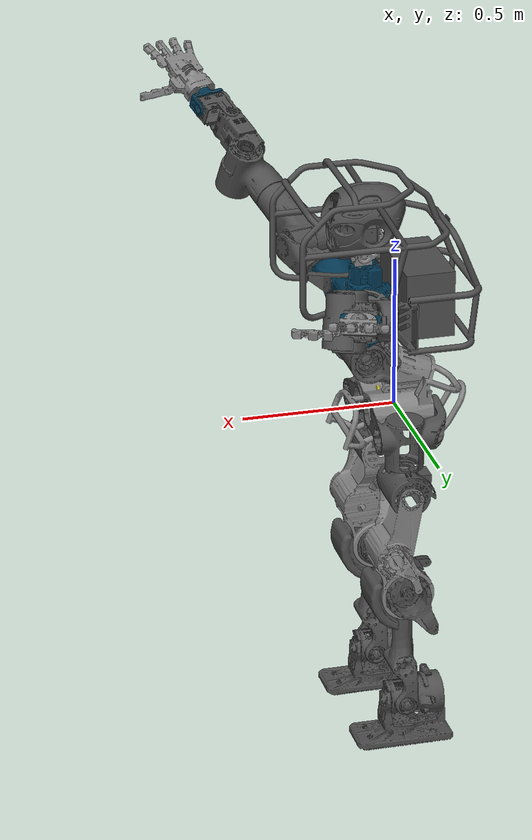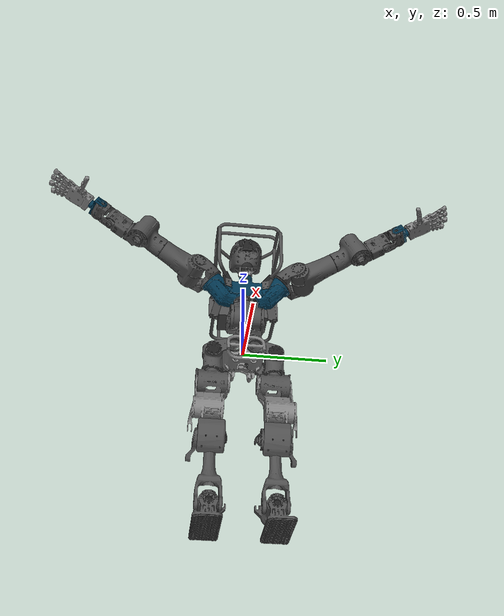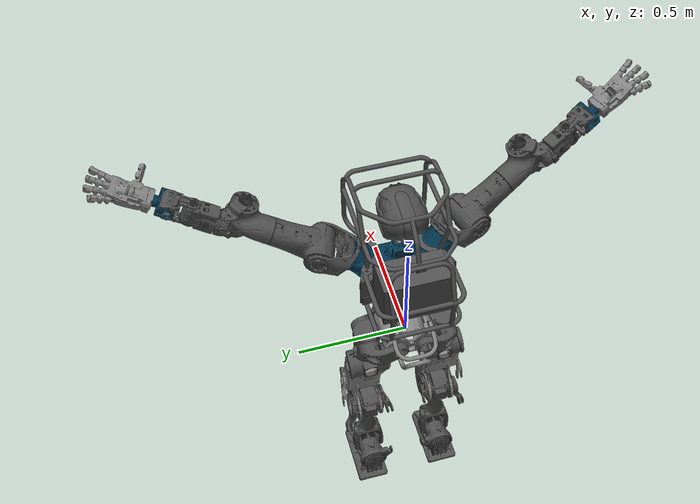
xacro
<?xml version="1.0"?>
<robot xmlns:xacro="http://ros.org/wiki/xacro" name="bigman">

<!-- ************ MODEL CONFIGURATION ************ -->
<xacro:include filename="bigman_config.urdf.xacro" />

<!-- ***********  MODEL COLORS *********** -->
<xacro:include filename="bigman_materials.urdf.xacro" />

<!-- ************ BIGMAN BASE ************** -->
<xacro:include filename="bigman_base.urdf.xacro"/>

<xacro:if value="${BIGMAN_LEGS}">
	<!-- ***** LEGS F/T SENSOR REF FRAMES *******-->
	<link name="l_leg_ft"/>
	<link name="r_leg_ft"/>

	<joint name="l_leg_ft_joint" type="fixed">
	    <parent link="LFoot"/>
	    <child link="l_leg_ft"/>
	    <origin xyz="0.005 0 -0.107" rpy="0 0 0"/>
	</joint>

	<joint name="r_leg_ft_joint" type="fixed">
	    <parent link="RFoot"/>
	    <child link="r_leg_ft"/>
	    <origin xyz="0.005 0 -0.107" rpy="0 0 0"/>
	</joint>
</xacro:if>

<xacro:if value="${BIGMAN_UPPER_BODY}">
	<link name="l_arm_ft"/>
	<link name="r_arm_ft"/>

	<joint name="l_arm_ft_joint" type="fixed">
	    <parent link="LWrMot3"/>
	    <child link="l_arm_ft"/>
	    <origin xyz="0 0 -0.0565" rpy="0 0 0" />
	</joint>

	<joint name="r_arm_ft_joint" type="fixed">
	    <parent link="RWrMot3"/>
	    <child link="r_arm_ft"/>
	    <origin xyz="0 0 -0.0565" rpy="0 0 0" />
	</joint>

	<!-- ************ FOREARMS ************ -->
	<!-- This links are defined in order to be compliant with http://www.ros.org/reps/rep-0120.html#coordinate-frames
	and to define the end effectors of the robot -->

	<!-- position and orientation of the arm regardless of the tool (grasping device for instance) attached to it -->
	<link name="l_wrist"/>
	<link name="r_wrist"/>

	<xacro:include filename="parts/forearms.urdf.xacro" />
       <xacro:if value="${BIGMAN_ADD_RAISING_SUPPORT}">
	       <xacro:include filename="parts/forearm_reference_frame.urdf.xacro" />
       </xacro:if>

	<!-- ************ HANDS ************ -->
	<xacro:include filename="parts/soft_hand.urdf.xacro" />

	<!-- multisense_sl_v4 with fixed joints -->
       <xacro:if value="${BIGMAN_HEAD}">
                <joint name="neck_joint" type="fixed">
                     <parent link="NeckPitch"/>
                     <child link="multisense/head"/>
                     <origin xyz="0.08765 0 0.06475" rpy="0 0 0" />
                 </joint>

              <xacro:unless value="${BIGMAN_FIXED_MULTISENSE}">
                     <xacro:include filename="sensors/multisense_sl_simulation.urdf.xacro"/>
              </xacro:unless>
              <xacro:if value="${BIGMAN_FIXED_MULTISENSE}">
                     <xacro:include filename="sensors/multisense_sl.urdf.xacro"/>
              </xacro:if>

       </xacro:if>
</xacro:if>

<xacro:if value="${BIGMAN_LEGS}">
	<!-- IMU -->
	<xacro:include filename="sensors/imu.urdf.xacro"/>
</xacro:if>

</robot>

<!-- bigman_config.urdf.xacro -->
<robot xmlns:xacro="http://ros.org/wiki/xacro" name="BIGMAN">

<xacro:property name="model_name" value="IIT Bigman Ctrl" />
<xacro:property name="model_version" value="0.1" />

<!--
####################################################
##
##  BIGMAN_YARP
##  if "true" the bigman robot is controlled via YARP
##
####################################################
-->
<xacro:property name="BIGMAN_YARP" value="false" />

<!--
####################################################
##
##  BIGMAN_XBOT
##  if "true" the bigman robot is controlled via
##  XBotCore Suite
##
####################################################
-->
<xacro:property name="BIGMAN_XBOT" value="true" />

<xacro:property name="BIGMAN_UPPER_BODY" value="true" />

<xacro:property name="BIGMAN_LEGS" value="true" />

<!--
####################################################
##
##  BIGMAN_OLD_CHEST
##  if "true" the old version of the chest will be
##  used.
##
##
####################################################
-->
<xacro:property name="BIGMAN_OLD_CHEST" value="false" />

<xacro:property name="BIGMAN_FIXED_HANDS" value="true" />

<xacro:property name="BIGMAN_FIXED_MULTISENSE" value="true" />

<xacro:property name="BIGMAN_HEAD" value="true" />

<!--
####################################################
##
##  BIGMAN_ADD_PROTECTIONS
##  if "true" the protections are added to the model.
##
##
####################################################
-->
<xacro:property name="BIGMAN_ADD_PROTECTIONS" value="true" />

<!--
####################################################
##
##  BIGMAN_ADD_BACKPACK
##  if "true" the backpack is added to the model.
##
##
####################################################
-->
<xacro:property name="BIGMAN_ADD_BACKPACK" value="true" />

<xacro:property name="BIGMAN_ADD_RAISING_SUPPORT" value="false" />

<xacro:property name="BIGMAN_NEW_FEET" value="true" />

<xacro:property name="BIGMAN_SAFETY_JOINT_LIMITS_ARMS" value="false" />
<xacro:property name="BIGMAN_SAFETY_JOINT_LIMITS_TORSO" value="false" />

</robot>

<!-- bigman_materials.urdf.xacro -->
<robot xmlns:xacro="http://ros.org/wiki/xacro">

<material name="grey">
  <color rgba="0.5 0.5 0.5 1"/>
</material>

<material name="dark_grey">
  <color rgba="0.3 0.3 0.3 1"/>
</material>

<material name="blue">
  <color rgba="0.0 0.2 0.3 1"/>
</material>

</robot>

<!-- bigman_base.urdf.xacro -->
<robot xmlns:xacro="http://ros.org/wiki/xacro">

<link name="base_link"/>

<link name="Waist">
    <inertial>
      <origin xyz="${-2.2813402e+01*mmTom} ${-7.3935443e-01*mmTom} ${3.0422909e+01*mmTom}" rpy="0.0 0.0 0.0"/>
      <mass value="1.1046081e+01"/>
      <inertia ixx="${9.6207978e+04*mm2Tom2}"  ixy="${1.4081043e+02*mm2Tom2}"  ixz="${3.1258127e+03*mm2Tom2}" iyy="${9.8511158e+04*mm2Tom2}" iyz="${1.3938149e+02*mm2Tom2}" izz="${8.6541531e+04*mm2Tom2}" />
    </inertial>
    <visual>
      <origin xyz="0 0 0" rpy="0 0 0"/>
      <geometry name="Waist_visual">
        <mesh filename="meshes/Waist.STL" scale="0.001 0.001 0.001"/>
      </geometry>
      <material name="grey"/>
    </visual>
    <collision>
      <origin xyz="0 0 0" rpy="0 0 0"/>
      <geometry name="Waist_collision">
        <mesh filename="meshes/simple/Waist.STL" scale="0.001 0.001 0.001"/>
      </geometry>
    </collision>
</link>

<joint name="base_joint" type="fixed">
    <parent link="base_link"/>
    <child link="Waist"/>
    <origin xyz="0 0 0" rpy="0 0 0" />
</joint>

<xacro:if value="${BIGMAN_LEGS}">
       <xacro:unless value="${BIGMAN_UPPER_BODY}">
		<!-- ********************FAKE TORSO******************** -->
		<xacro:include filename="parts/pelvis_weight_bench.urdf.xacro" />
       </xacro:unless>
</xacro:if>

<xacro:if value="${BIGMAN_UPPER_BODY}">
       <!-- ********************TORSO******************** -->
       <!-- first real link of the robot, inertial reference frame -->
       <xacro:include filename="parts/torso.urdf.xacro" />

       <!-- ********************NECK********************* -->
       <xacro:include filename="parts/neck.urdf.xacro" />
</xacro:if>

<xacro:if value="${BIGMAN_LEGS}">
	<!-- ********************LEGS******************** -->
	<!-- This links are defined in order to be compliant with http://www.ros.org/reps/rep-0120.html#coordinate-frames
	and to define the end effectors of the robot -->

	<!--  position and orientation of the leg regardless of the support body geometry -->
	  <link name="l_ankle"/>
	  <link name="r_ankle"/>

	  <link name="l_sole"/>
	  <link name="r_sole"/>

	  <link name="l_toe"/>
	  <link name="r_toe"/>

	<xacro:include filename="parts/legs.urdf.xacro" />

  	<joint name="l_ankle_joint" type="fixed">
	     <parent link="LFoot"/>
	     <child link="l_ankle"/>
	     <origin xyz="0 0 0" rpy="0 0 0" />
        </joint>

	  <joint name="r_ankle_joint" type="fixed">
	    <parent link="RFoot"/>
	    <child link="r_ankle"/>
	    <origin xyz="0 0 0" rpy="0 0 0" />
	  </joint>

	  <joint name="l_sole_joint" type="fixed">
	    <parent link="LFoot"/>
	    <child link="l_sole"/>
	    <origin xyz="0 0 -0.1435" rpy="0 0 0" />
	  </joint>

	  <joint name="r_sole_joint" type="fixed">
	    <parent link="RFoot"/>
	    <child link="r_sole"/>
	    <origin xyz="0 0 -0.1435" rpy="0 0 0" />
	  </joint>

	  <joint name="l_toe_joint" type="fixed">
	    <parent link="l_sole"/>
	    <child link="l_toe"/>
           <xacro:unless value="${BIGMAN_NEW_FEET}">
	      <origin xyz="0.195 0 0" rpy="0 0 0" />
           </xacro:unless>
           <xacro:if value="${BIGMAN_NEW_FEET}">
	      <origin xyz="0.16 0 0" rpy="0 0 0" />
           </xacro:if>
	  </joint>

	  <joint name="r_toe_joint" type="fixed">
	    <parent link="r_sole"/>
	    <child link="r_toe"/>
	    <xacro:unless value="${BIGMAN_NEW_FEET}">
	      <origin xyz="0.195 0 0" rpy="0 0 0" />
           </xacro:unless>
           <xacro:if value="${BIGMAN_NEW_FEET}">
	      <origin xyz="0.16 0 0" rpy="0 0 0" />
           </xacro:if>
	  </joint>

	<!-- Reference frames in feet -->
	<xacro:include filename="parts/foot_reference_frame.urdf.xacro" />
</xacro:if>

<xacro:if value="${BIGMAN_UPPER_BODY}">
       <!-- ********************ARMS******************** -->
       <xacro:include filename="parts/arms.urdf.xacro" />
</xacro:if>

</robot>

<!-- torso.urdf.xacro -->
<robot xmlns:xacro="http://ros.org/wiki/xacro">

<xacro:property name="mmTom" value="0.001" />
<xacro:property name="mm2Tom2" value="${0.001*0.001}" />

<xacro:property name="PI" value="3.14159265359" />
<xacro:property name="PI_2" value="1.57079632679" />
<xacro:property name="SF" value="0.03937" /> <!-- Scale factor for meshes -->

<xacro:property name="cos_26" value="0.89879991307" />
<xacro:property name="sin_26" value="0.43835911792" />

<xacro:property name="toRad" value="${PI/180.0}" />

<!-- LINKS -->
<!-- This links are defined in order to be compliant with http://www.ros.org/reps/rep-0120.html#coordinate-frames
and to define the end effectors of the robot-->

<!-- The coordinate frame called torso is attached to the lowest body of the model which is a parent of l_gripper, r_gripper and gaze. -->
 <link name="torso"/>

  <link name ="DWL">
    <inertial>
      <origin xyz="-0.04610869 0.02232230 -0.02249514" rpy="0 0 0"/>
      <mass value="1.44965471"/>
      <inertia ixx="0.01096760"  ixy="0.00111556"  ixz="0.00030030" iyy="0.00409572" iyz="0.00054456" izz="0.01143795" />
    </inertial>
    <visual>
      <origin xyz="0.0 0.0 0.0" rpy="0 0 0"/>
      <geometry name="DWL_visual">
        <mesh filename="meshes/TorsoRoll.STL" scale="0.001 0.001 0.001" />
      </geometry>
      <material name="dark_grey"/>
    </visual>
    <collision>
      <origin xyz="0.0 0.0 0.0" rpy="0 0 0"/>
      <geometry name="DWL_collision">
        <mesh filename="meshes/simple/TorsoRoll.STL" scale="0.001 0.001 0.001" />
      </geometry>
    </collision>
  </link>

  <link name ="DWS">
    <inertial>
      <origin xyz="0.00010203 0.00928164 0.08113610" rpy="0 0 0"/>
      <mass value="5.28825567"/>
      <inertia ixx="0.01628069"  ixy="-0.00000323"  ixz="0.00001424" iyy="0.01424286" iyz="0.00075458" izz="0.00994169" />
    </inertial>
    <visual>
      <origin xyz="0.0 0.0 0.0" rpy="0 0 0"/>
      <geometry name="DWS_visual">
        <mesh filename="meshes/TorsoYawPitch.STL" scale="0.001 0.001 0.001" />
      </geometry>
      <material name="dark_grey"/>
    </visual>
    <collision>
      <origin xyz="0.0 0.0 0.0" rpy="0 0 0"/>
      <geometry name="DWS_collision">
        <mesh filename="meshes/simple/TorsoYawPitch.STL" scale="0.001 0.001 0.001" />
      </geometry>
    </collision>
  </link>

  <link name ="DWYTorso">
    <inertial>
        <origin xyz="0.0 0.00 0.3" rpy="0 0 0"/>
        <mass value="26"/>
      <inertia ixx="0.18629757"  ixy="0.00008160"  ixz="0.00030250" iyy="0.02013829" iyz="-0.00001790" izz="0.18850541" />
    </inertial>
    <visual>
      <origin xyz="0.0 0.0 0.0" rpy="0 0 0"/>
      <geometry name="DWYTorso_visual">
<xacro:if value="${BIGMAN_OLD_CHEST}">
        <mesh filename="meshes/Chest.STL" scale="0.001 0.001 0.001" />
</xacro:if>
<xacro:unless value="${BIGMAN_OLD_CHEST}">
        <mesh filename="meshes/NewChest.STL" scale="0.001 0.001 0.001" />
</xacro:unless>
      </geometry>
      <material name="blue"/>
    </visual>
    <collision>
      <origin xyz="0.0 0.0 0.0" rpy="0 0 0"/>
      <geometry name="DWYTorso_collision">
<xacro:if value="${BIGMAN_OLD_CHEST}">
        <mesh filename="meshes/simple/Chest.STL" scale="0.001 0.001 0.001" />
</xacro:if>
<xacro:unless value="${BIGMAN_OLD_CHEST}">
        <mesh filename="meshes/simple/NewChest.STL" scale="0.001 0.001 0.001" />
</xacro:unless>
      </geometry>
    </collision>
  </link>

<!-- UPDATE DATA FOR TORSO PROTECTION! -->
<xacro:if value="${BIGMAN_ADD_PROTECTIONS}">
<link name ="TorsoProtections">
    <inertial>
      <origin xyz="${-8.2963193e+01*mmTom} ${7.0747291e-04*mmTom} ${7.5409106e+01*mmTom}" rpy="0 0 0"/>
      <mass value="4.7"/>
      <inertia ixx="${1.4773769e+05*mm2Tom2}"  ixy="${0.0*mm2Tom2}"  ixz="${-2.9780072e+04*mm2Tom2}" iyy="${1.6085511e+05*mm2Tom2}" iyz="${0.0*mm2Tom2}" izz="${1.5409381e+05*mm2Tom2}" />
    </inertial>
    <visual>
      <origin xyz="0.0 0.0 0.0" rpy="0 0 0"/>
      <geometry name="TorsoProtections_visual">
        <mesh filename="meshes/ProtectionSystem.STL" scale="0.001 0.001 0.001" />
      </geometry>
      <material name="dark_grey"/>
    </visual>
    <collision>
      <origin xyz="0.0 0.0 0.0" rpy="0 0 0"/>
      <geometry name="TorsoProtections_collision">
        <mesh filename="meshes/simple/ProtectionSystem.STL" scale="0.001 0.001 0.001" />
      </geometry>
    </collision>
  </link>
</xacro:if>

<!-- UPDATE DATA FOR TORSO PROTECTION! -->
<xacro:if value="${BIGMAN_ADD_BACKPACK}">
<link name="backpack">
    <inertial>
      <origin xyz="0 0 -0.065" rpy="0 0 0"/>
      <mass value="10.0"/>
      <inertia ixx="${(10.0/12.0)*(0.3*0.3+0.13*0.13)}"  ixy="0.0"  ixz="0.0" iyy="${(10.0/12.0)*(0.16*0.16+0.13*0.13)}" iyz="0.0" izz="${(10.0/12.0)*(0.16*0.16+0.3*0.3)}" />
    </inertial>
    <visual>
      <origin xyz="0.0 0.0 0.0" rpy="0 0 0"/>
      <geometry name="backpack_visual">
        <box size="0.16 0.3 0.22" />
      </geometry>
      <material name="dark_grey"/>
    </visual>
    <collision>
      <origin xyz="0.0 0.0 0.0" rpy="0 0 0"/>
      <geometry name="backpack_collision">
        <box size="0.16 0.3 0.22" />
      </geometry>
    </collision>
</link>
</xacro:if>

<!-- JOINTS -->
<xacro:if value="${BIGMAN_ADD_BACKPACK}">
<joint name="backpack_joint" type="fixed">
    <parent link="DWYTorso"/>
    <child link="backpack"/>
    <origin xyz="-0.185 0 -0.025" rpy="0 0 0" />
</joint>
</xacro:if>

<xacro:if value="${BIGMAN_ADD_PROTECTIONS}">
<joint name="torso_protection_joint" type="fixed">
    <parent link="DWYTorso"/>
    <child link="TorsoProtections"/>
    <origin xyz="0.0 0 0.0" rpy="0 0 0" />
</joint>
</xacro:if>

<joint name="torso_joint" type="fixed">
    <parent link="DWYTorso"/>
    <child link="torso"/>
    <origin xyz="0.0 0 0.0" rpy="0 0 0" />
</joint>

<joint name="WaistLat" type="revolute">
    <parent link="Waist"/>
    <child link="DWL"/>
    <origin xyz="0.1115 0 0.195982" rpy="0 0 0" />
    <axis xyz="${cos_26} 0 ${sin_26}" />
    <xacro:if value="${BIGMAN_SAFETY_JOINT_LIMITS_TORSO}">
    	<limit velocity="6.283" effort="120" lower="${-15.0*toRad}" upper="${15.0*toRad}" />
    </xacro:if>
    <xacro:unless value="${BIGMAN_SAFETY_JOINT_LIMITS_TORSO}">
    	<limit velocity="6.283" effort="120" lower="${-35.0*toRad}" upper="${35.0*toRad}" />
    </xacro:unless>
    <dynamics friction="0" damping="3.0"/>
</joint>

  <joint name="WaistSag" type="revolute">
    <parent link="DWL"/>
    <child link="DWS"/>
    <origin xyz="0 0 0" rpy="0 0 0" />
    <axis xyz="0 1 0" />
    <xacro:if value="${BIGMAN_SAFETY_JOINT_LIMITS_TORSO}">
    	<limit velocity="6.283" effort="220" lower="${-10.0*toRad}" upper="${40.0*toRad}" />
    </xacro:if>
    <xacro:unless value="${BIGMAN_SAFETY_JOINT_LIMITS_TORSO}">
    	<limit velocity="6.283" effort="220" lower="${-20.0*toRad}" upper="${80.0*toRad}" />
    </xacro:unless>
    <dynamics friction="0" damping="3.0"/>
  </joint>

  <joint name="WaistYaw" type="revolute">
    <parent link="DWS"/>
    <child link="DWYTorso"/>
    <origin xyz="0 0 0.22275" rpy="0 0 0" />
    <axis xyz="0 0 1" />
    <xacro:if value="${BIGMAN_SAFETY_JOINT_LIMITS_TORSO}">
    	<limit velocity="6.283" effort="120" lower="${-100.0*toRad}" upper="${100.0*toRad}" />
    </xacro:if>
    <xacro:unless value="${BIGMAN_SAFETY_JOINT_LIMITS_TORSO}">
    	<limit velocity="6.283" effort="120" lower="${-163.0*toRad}" upper="${163.0*toRad}" />
    </xacro:unless>
    <dynamics friction="0" damping="3.0"/>
  </joint>

</robot>

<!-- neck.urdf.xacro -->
<robot xmlns:xacro="http://ros.org/wiki/xacro">

<xacro:property name="mmTom" value="0.001" />
<xacro:property name="mm2Tom2" value="${0.001*0.001}" />

<xacro:property name="PI" value="3.14159265359" />
<xacro:property name="PI_2" value="1.57079632679" />

<xacro:property name="cos_26" value="0.89879991307" />
<xacro:property name="sin_26" value="0.43835911792" />

<xacro:property name="toRad" value="${PI/180.0}" />

<!-- LINKS -->
  <link name ="NeckYaw">
    <inertial>
      <origin xyz="0.0 0.0 ${1.1550000e+02*mmTom}" rpy="0 0 0"/>
      <mass value="0.35"/>
      <inertia ixx="${3.2840119e+02*mm2Tom2}"  ixy="0.0"  ixz="0.0" iyy="${7.0371675e+01*mm2Tom2}" iyz="0.0" izz="${3.2840111e+02*mm2Tom2}" />
    </inertial>
    <visual>
      <origin xyz="0.0 0.0 0.0" rpy="0 0 0"/>
      <geometry name="NeckYaw_visual">
        <mesh filename="meshes/NeckYaw.STL" scale="0.001 0.001 0.001" />
      </geometry>
      <material name="grey"/>
    </visual>
    <collision>
      <origin xyz="0.0 0.0 0.0" rpy="0 0 0"/>
      <geometry name="NeckYaw_collision">
        <mesh filename="meshes/simple/NeckYaw.STL" scale="0.001 0.001 0.001" />
      </geometry>
    </collision>
  </link>

  <link name ="NeckPitch">
    <inertial>
      <origin xyz="${-1.020e+02*mmTom} 0.0 ${2.6575000e+02*mmTom}" rpy="0 0 0"/>
      <mass value="0.623"/>
      <inertia ixx="${1.0388333e+03*mm2Tom2}"  ixy="0.0"  ixz="0.0" iyy="${5.4689381e+02*mm2Tom2}" iyz="0.0" izz="${5.4689381e+02*mm2Tom2}" />
    </inertial>
    <visual>
      <origin xyz="0.0 0.0 0.0" rpy="0 0 0"/>
      <geometry name="NeckPitch_visual">
        <mesh filename="meshes/NeckPitch.STL" scale="0.001 0.001 0.001" />
      </geometry>
      <material name="grey"/>
    </visual>
    <collision>
      <origin xyz="0.0 0.0 0.0" rpy="0 0 0"/>
      <geometry name="NeckPitch_collision">
        <mesh filename="meshes/simple/NeckPitch.STL" scale="0.001 0.001 0.001" />
      </geometry>
    </collision>
  </link>

<!-- JOINTS -->
<joint name="NeckYawj" type="revolute">
    <parent link="DWYTorso"/>
    <child link="NeckYaw"/>
    <origin xyz="0 0 0" rpy="0 0 0" />
    <axis xyz="0 0 1" />
    <limit velocity="6.283" effort="120" lower="${(-35.0)*toRad}" upper="${(35.0)*toRad}" />
    <dynamics friction="0" damping="3.0"/>
</joint>

<joint name="NeckPitchj" type="revolute">
    <parent link="NeckYaw"/>
    <child link="NeckPitch"/>
    <origin xyz="0 0 0.117" rpy="0 0 0" />
    <axis xyz="0 1 0" />
    <!--limit velocity="6.283" effort="120" lower="${(-30.0)*toRad}" upper="${(70.0)*toRad}" /-->
    <limit velocity="6.283" effort="120" lower="${(-15.0)*toRad}" upper="${(60.0)*toRad}" />
    <dynamics friction="0" damping="3.0"/>
</joint>

</robot>

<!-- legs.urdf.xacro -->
<robot xmlns:xacro="http://ros.org/wiki/xacro">

<xacro:property name="mmTom" value="0.001" />
<xacro:property name="mm2Tom2" value="${0.001*0.001}" />
<xacro:property name="tonsToKg" value="1000.0" />

<xacro:property name="PI" value="3.14159265359" />
<xacro:property name="PI_2" value="1.57079632679" />

<!-- LINKS -->

<!-- ********************RIGHT LEG******************** -->

<link name ="RHipMot">
    <inertial>
      <origin xyz="${-1.0348188e+02*mmTom} ${-1.0919813e+02*mmTom} ${-6.4924056e+01*mmTom}" rpy="0 0 0"/>
      <mass value="${3.7958197e-03*tonsToKg}"/>
      <inertia ixx="${1.5639017e+01*mm2Tom2*tonsToKg}"  ixy="${1.8504661*mm2Tom2*tonsToKg}"  ixz="${2.3907793*mm2Tom2*tonsToKg}" iyy="${2.3519749e+01*mm2Tom2*tonsToKg}" iyz="${-2.3303162*mm2Tom2*tonsToKg}" izz="${2.0953643e+01*mm2Tom2*tonsToKg}" />
    </inertial>
    <visual>
      <origin xyz="0 0 0" rpy="0 0 0"/>
      <geometry name="RHipMot_visual">
        <mesh filename="meshes/HipRoll.STL" scale="0.001 0.001 0.001" />
      </geometry>
      <material name="dark_grey"/>
    </visual>
    <collision>
      <origin xyz="0 0 0" rpy="0 0 0"/>
      <geometry name="RHipMot_collision">
        <mesh filename="meshes/simple/HipRoll.STL" scale="0.001 0.001 0.001" />
      </geometry>
    </collision>
</link>

  <link name ="RThighUpLeg">
    <inertial>
      <origin xyz="${-5.2929709*mmTom} ${-2.2561833e+01*mmTom} ${5.6701669*mmTom}" rpy="0 0 0"/>
      <mass value="3.2402068"/>
      <inertia ixx="${1.0102097e+04*mm2Tom2}"  ixy="${1.0858487e+02*mm2Tom2}"  ixz="${2.5291395e+02*mm2Tom2}" iyy="${6.7147000e+03*mm2Tom2}" iyz="${8.3447072e+01*mm2Tom2}" izz="${1.0485130e+04*mm2Tom2}" />
    </inertial>
    <visual>
      <origin xyz="0 0 0" rpy="0 0 0"/>
      <geometry name="RThighUpLeg_visual">
        <mesh filename="meshes/HipYaw.STL" scale="0.001 0.001 0.001" />
      </geometry>
      <material name="dark_grey"/>
    </visual>
    <collision>
      <origin xyz="0 0 0" rpy="0 0 0"/>
      <geometry name="RThighUpLeg_collision">
        <mesh filename="meshes/simple/HipYaw.STL" scale="0.001 0.001 0.001" />
      </geometry>
    </collision>
  </link>

  <link name ="RThighLowLeg">
    <inertial>
      <origin xyz="${3.7746286e+01*mmTom} ${-2.8539939e+01*mmTom} ${-1.9310133e+02*mmTom}" rpy="0 0 0"/>
      <mass value="5.0950736"/>
      <inertia ixx="${5.1607858e+04*mm2Tom2}"  ixy="${2.2253472e+03*mm2Tom2}"  ixz="${2.4529790e+03*mm2Tom2}" iyy="${4.4349153e+04*mm2Tom2}" iyz="${-4.1006942e+03*mm2Tom2}" izz="${2.3374453e+04*mm2Tom2}" />
    </inertial>
    <visual>
      <origin xyz="0 0 0" rpy="0 0 0"/>
      <geometry name="RThighLowLeg_visual">
        <mesh filename="meshes/HipPitch.STL" scale="0.001 0.001 0.001" />
      </geometry>
      <material name="grey"/>
    </visual>
    <collision>
      <origin xyz="0 0 0" rpy="0 0 0"/>
      <geometry name="RThighLowLeg_collision">
        <mesh filename="meshes/simple/HipPitch.STL" scale="0.001 0.001 0.001" />
      </geometry>
    </collision>
  </link>

  <link name ="RLowLeg">
    <inertial>
      <origin xyz="${-5.0828668*mmTom} ${3.7732093*mmTom} ${-7.2605017e+01*mmTom}" rpy="0 0 0"/>
      <mass value="5.6495309"/>
      <inertia ixx="${1.0535542e+05*mm2Tom2}"  ixy="${-5.8199221e+02*mm2Tom2}"  ixz="${1.6743598e+03*mm2Tom2}" iyy="${9.7857796e+04*mm2Tom2}" iyz="${-3.3770181e+03*mm2Tom2}" izz="${2.0854086e+04*mm2Tom2}" />
    </inertial>
    <visual>
      <origin xyz="0 0 0" rpy="0 0 0"/>
      <geometry name="RLowLeg_visual">
        <mesh filename="meshes/KneePitchCalf.STL" scale="0.001 0.001 0.001" />
      </geometry>
      <material name="dark_grey"/>
    </visual>
    <collision>
      <origin xyz="0 0 0" rpy="0 0 0"/>
      <geometry name="RLowLeg_collision">
        <mesh filename="meshes/simple/KneePitchCalf.STL" scale="0.001 0.001 0.001" />
      </geometry>
    </collision>
  </link>

  <link name ="RFootmot">
    <inertial>
      <origin xyz="${-2.2024173e+01*mmTom} ${2.5677238*mmTom} ${9.4588455e-01*mmTom}" rpy="0 0 0"/>
      <mass value="3.2844159"/>
      <inertia ixx="${7.5550679e+03*mm2Tom2}"  ixy="${6.7488292e+02*mm2Tom2}"  ixz="${5.8332889e+01*mm2Tom2}" iyy="${1.1241163e+04*mm2Tom2}" iyz="${-1.4552081e+02*mm2Tom2}" izz="${1.3391865e+04*mm2Tom2}" />
    </inertial>
    <visual>
      <origin xyz="0 0 0" rpy="0 0 0"/>
      <geometry name="RFootmot_visual">
        <mesh filename="meshes/AnklePitch.STL" scale="0.001 0.001 0.001" />
      </geometry>
      <material name="dark_grey"/>
    </visual>
    <collision>
      <origin xyz="0 0 0" rpy="0 0 0"/>
      <geometry name="RFootmot_collision">
        <mesh filename="meshes/simple/AnklePitch.STL" scale="0.001 0.001 0.001" />
      </geometry>
    </collision>
  </link>

  <link name ="RFoot">
     <inertial>
        <xacro:if value="${BIGMAN_NEW_FEET}">
          <origin xyz="-0.00653584 -0.00479384 -0.10180375" rpy="0 0 0"/>
          <mass value="3.42638110"/>
          <inertia ixx="0.01032886"  ixy="-0.00016407"  ixz="-0.00201294" iyy="0.02854025" iyz="0.00046315" izz="0.02799499" />
        </xacro:if>
        <xacro:unless value="${BIGMAN_NEW_FEET}">
          <origin xyz="0.01282904 -0.00463694 -0.10109499" rpy="0 0 0"/>
          <mass value="3.33109981"/>
          <inertia ixx="0.01006627"  ixy="-0.00051955"  ixz="-0.00374069" iyy="0.02882577" iyz="0.00044505" izz="0.02819025" />
        </xacro:unless>
      </inertial>
    <visual>
      <origin xyz="0 0 0" rpy="0 0 0"/>
      <geometry name="RFoot_visual">
        <xacro:if value="${BIGMAN_NEW_FEET}">
              <mesh filename="meshes/NewFoot.STL" scale="0.001 0.001 0.001"/>
        </xacro:if>
        <xacro:unless value="${BIGMAN_NEW_FEET}">
              <mesh filename="meshes/Foot.STL" scale="0.001 -0.001 0.001"/>
        </xacro:unless>
      </geometry>
      <material name="dark_grey"/>
    </visual>
    <collision>
     <xacro:if value="${BIGMAN_NEW_FEET}">
       <origin xyz="0.005 -0.01 -0.1359" rpy="0 0 0"/>
       <geometry>
         <box size="0.32 0.16 0.015" />
       </geometry>
     </xacro:if>
     <xacro:unless value="${BIGMAN_NEW_FEET}">
       <origin xyz="0.047 -0.01 -0.1359" rpy="0 0 0"/>
       <geometry>
         <box size="0.306 0.16 0.015" />
       </geometry>
     </xacro:unless>
    </collision>
  </link>

<!-- ********************LEFT LEG******************** -->
  <link name ="LHipMot">
    <inertial>
      <origin xyz="${-1.0348188e+02*mmTom} ${1.0919813e+02*mmTom} ${-6.4924056e+01*mmTom}" rpy="0 0 0"/>
      <mass value="${3.7958197e-03*tonsToKg}"/>
      <inertia ixx="${1.5639017e+01*mm2Tom2*tonsToKg}"  ixy="${-1.8504661*mm2Tom2*tonsToKg}"  ixz="${2.3907793*mm2Tom2*tonsToKg}" iyy="${2.3519749e+01*mm2Tom2*tonsToKg}" iyz="${2.3303162*mm2Tom2*tonsToKg}" izz="${2.0953643e+01*mm2Tom2*tonsToKg}" />
    </inertial>
    <visual>
      <origin xyz="0 0 0" rpy="0 0 0"/>
      <geometry name="LHipMot_visual">
        <mesh filename="meshes/HipRoll.STL" scale="0.001 -0.001 0.001" />
      </geometry>
      <material name="dark_grey"/>
    </visual>
    <collision>
      <origin xyz="0 0 0" rpy="0 0 0"/>
      <geometry name="LHipMot_collision">
        <mesh filename="meshes/simple/HipRoll.STL" scale="0.001 -0.001 0.001" />
      </geometry>
    </collision>
  </link>

  <link name ="LThighUpLeg">
    <inertial>
      <origin xyz="${-5.2929709*mmTom} ${2.2561833e+01*mmTom} ${5.6701669*mmTom}" rpy="0 0 0"/>
      <mass value="3.2402068"/>
      <inertia ixx="${1.0102097e+04*mm2Tom2}"  ixy="${-1.0858487e+02*mm2Tom2}"  ixz="${2.5291395e+02*mm2Tom2}" iyy="${6.7147000e+03*mm2Tom2}" iyz="${-8.3447072e+01*mm2Tom2}" izz="${1.0485130e+04*mm2Tom2}" />
    </inertial>
    <visual>
      <origin xyz="0 0 0" rpy="0 0 0"/>
      <geometry name="LThighUpLeg_visual">
        <mesh filename="meshes/HipYaw.STL" scale="0.001 -0.001 0.001" />
      </geometry>
      <material name="dark_grey"/>
    </visual>
    <collision>
      <origin xyz="0 0 0" rpy="0 0 0"/>
      <geometry name="LThighUpLeg_collision">
        <mesh filename="meshes/simple/HipYaw.STL" scale="0.001 -0.001 0.001" />
      </geometry>
    </collision>
  </link>

  <link name ="LThighLowLeg">
    <inertial>
      <origin xyz="${3.7746286e+01*mmTom} ${2.8539939e+01*mmTom} ${-1.9310133e+02*mmTom}" rpy="0 0 0"/>
      <mass value="5.0950736"/>
      <inertia ixx="${5.1607858e+04*mm2Tom2}"  ixy="${-2.2253472e+03*mm2Tom2}"  ixz="${2.4529790e+03*mm2Tom2}" iyy="${4.4349153e+04*mm2Tom2}" iyz="${4.1006942e+03*mm2Tom2}" izz="${2.3374453e+04*mm2Tom2}" />
    </inertial>
    <visual>
      <origin xyz="0 0 0" rpy="0 0 0"/>
      <geometry name="LThighLowLeg_visual">
        <mesh filename="meshes/HipPitch.STL" scale="0.001 -0.001 0.001" />
      </geometry>
      <material name="grey"/>
    </visual>
    <collision>
      <origin xyz="0 0 0" rpy="0 0 0"/>
      <geometry name="LThighLowLeg_collision">
        <mesh filename="meshes/simple/HipPitch.STL" scale="0.001 -0.001 0.001" />
      </geometry>
    </collision>
  </link>

  <link name ="LLowLeg">
    <inertial>
      <origin xyz="${-5.0828668*mmTom} ${-3.7732093*mmTom} ${-7.2605017e+01*mmTom}" rpy="0 0 0"/>
      <mass value="5.6495309"/>
      <inertia ixx="${1.0535542e+05*mm2Tom2}"  ixy="${5.8199221e+02*mm2Tom2}"  ixz="${1.6743598e+03*mm2Tom2}" iyy="${9.7857796e+04*mm2Tom2}" iyz="${3.3770181e+03*mm2Tom2}" izz="${2.0854086e+04*mm2Tom2}" />
    </inertial>
    <visual>
      <origin xyz="0 0 0" rpy="0 0 0"/>
      <geometry name="LLowLeg_visual">
        <mesh filename="meshes/KneePitchCalf.STL" scale="0.001 -0.001 0.001" />
      </geometry>
      <material name="dark_grey"/>
    </visual>
    <collision>
      <origin xyz="0 0 0" rpy="0 0 0"/>
      <geometry name="LLowLeg_collision">
        <mesh filename="meshes/simple/KneePitchCalf.STL" scale="0.001 -0.001 0.001" />
      </geometry>
    </collision>
  </link>

  <link name ="LFootmot">
    <inertial>
      <origin xyz="${-2.2024173e+01*mmTom} ${-2.5677238*mmTom} ${9.4588455e-01*mmTom}" rpy="0 0 0"/>
      <mass value="3.2844159"/>
      <inertia ixx="${7.5550679e+03*mm2Tom2}"  ixy="${-6.7488292e+02*mm2Tom2}"  ixz="${5.8332889e+01*mm2Tom2}" iyy="${1.1241163e+04*mm2Tom2}" iyz="${1.4552081e+02*mm2Tom2}" izz="${1.3391865e+04*mm2Tom2}" />
    </inertial>
    <visual>
      <origin xyz="0 0 0" rpy="0 0 0"/>
      <geometry name="LFootmot_visual">
        <mesh filename="meshes/AnklePitch.STL" scale="0.001 -0.001 0.001" />
      </geometry>
      <material name="dark_grey"/>
    </visual>
    <collision>
      <origin xyz="0 0 0" rpy="0 0 0"/>
      <geometry name="LFootmot_collision">
        <mesh filename="meshes/simple/AnklePitch.STL" scale="0.001 -0.001 0.001" />
      </geometry>
    </collision>
  </link>

  <link name ="LFoot">
      <inertial>
        <xacro:if value="${BIGMAN_NEW_FEET}">
          <origin xyz="-0.00653584 0.00479384 -0.10180375" rpy="0 0 0"/>
          <mass value="3.42638110"/>
          <inertia ixx="0.01032886"  ixy="0.00016407"  ixz="-0.00201294" iyy="0.02854025" iyz="-0.00046315" izz="0.02799499" />
        </xacro:if>
        <xacro:unless value="${BIGMAN_NEW_FEET}">
          <origin xyz="0.01282904 0.00463694 -0.10109499" rpy="0 0 0"/>
          <mass value="3.33109981"/>
          <inertia ixx="0.01006627"  ixy="0.00051955"  ixz="-0.00374069" iyy="0.02882577" iyz="-0.00044505" izz="0.02819025" />
        </xacro:unless>
      </inertial>
      <visual>
      <origin xyz="0 0 0" rpy="0 0 0"/>
      <geometry name="LFoot_visual">
        <xacro:if value="${BIGMAN_NEW_FEET}">
              <mesh filename="meshes/NewFoot.STL" scale="0.001 -0.001 0.001"/>
        </xacro:if>
        <xacro:unless value="${BIGMAN_NEW_FEET}">
              <mesh filename="meshes/Foot.STL" scale="0.001 0.001 0.001"/>
        </xacro:unless>
      </geometry>
      <material name="dark_grey"/>
    </visual>
    <collision>
     <xacro:if value="${BIGMAN_NEW_FEET}">
       <origin xyz="0.005 0.01 -0.1359" rpy="0 0 0"/>
       <geometry>
        <box size="0.32 0.16 0.015" />
       </geometry>
     </xacro:if>
     <xacro:unless value="${BIGMAN_NEW_FEET}">
       <origin xyz="0.047 0.01 -0.1359" rpy="0 0 0"/>
       <geometry>
        <box size="0.306 0.16 0.015" />
       </geometry>
     </xacro:unless>
    </collision>
   </link>

<!-- JOINTS -->

<!-- ********************RIGHT LEG******************** -->

  <joint name="RHipLat" type="revolute">
    <parent link="Waist"/>
    <child link="RHipMot"/>
    <origin xyz="0.1059 -0.06 0.0" rpy="0 0 0" />
    <axis xyz="1 0 0" />
    <limit velocity="6.283" effort="400" lower="-0.87222" upper="0.697778" />
    <dynamics friction="0" damping="3.0"/>
  </joint>

  <joint name="RHipYaw" type="revolute">
    <parent link="RHipMot"/>
    <child link="RThighUpLeg"/>
    <origin xyz="-0.0889 -0.121032 -0.217872" rpy="0 0 0" />
    <axis xyz="0 0 1" />
    <limit velocity="6.283" effort="140" lower="-1.57" upper="0.872222" />
    <dynamics friction="0" damping="3.0"/>
  </joint>

  <joint name="RHipSag" type="revolute">
    <parent link="RThighUpLeg"/>
    <child link="RThighLowLeg"/>
    <origin xyz="0.0 0.0 0.0" rpy="0 0 0" />
    <axis xyz="0 1 0" />
    <limit velocity="6.283" effort="400" lower="-2.09333" upper="1.046667" />
    <dynamics friction="0" damping="3.0"/>
  </joint>

  <joint name="RKneeSag" type="revolute">
    <parent link="RThighLowLeg"/>
    <child link="RLowLeg"/>
    <origin xyz="0.0 0.0 -0.356" rpy="0 0 0" />
    <axis xyz="0 1 0" />
    <limit velocity="6.283" effort="400" lower="0.0" upper="2.442222" />
    <dynamics friction="0" damping="3.0"/>
  </joint>

  <joint name="RAnkSag" type="revolute">
    <parent link="RLowLeg"/>
    <child link="RFootmot"/>
    <origin xyz="0.0 0.0 -0.4" rpy="0 0 0" />
    <axis xyz="0 1 0" />
    <limit velocity="6.283" effort="330" lower="-1.39556" upper="0.697778" />
    <dynamics friction="0" damping="3.0"/>
  </joint>

    <joint name="RAnkLat" type="revolute">
      <parent link="RFootmot"/>
      <child link="RFoot"/>
      <origin xyz="0.0 0.0 0.0" rpy="0 0 0" />
      <axis xyz="1 0 0" />
      <limit velocity="6.283" effort="210" lower="-0.785" upper="0.785" />
      <dynamics friction="0" damping="3.0"/>
    </joint>

<!-- ********************LEFT LEG******************** -->

  <joint name="LHipLat" type="revolute">
    <parent link="Waist"/>
    <child link="LHipMot"/>
    <origin xyz="0.1059 0.06 0.0" rpy="0 0 0" />
    <axis xyz="1 0 0" />
    <limit velocity="6.283" effort="400" lower="-0.697778" upper="0.87222" />
    <dynamics friction="0" damping="3.0"/>
  </joint>

  <joint name="LHipYaw" type="revolute">
    <parent link="LHipMot"/>
    <child link="LThighUpLeg"/>
    <origin xyz="-0.0889 0.121032 -0.217872" rpy="0 0 0" />
    <axis xyz="0 0 1" />
    <limit velocity="6.283" effort="140" lower="-0.872222" upper="1.57" />
    <dynamics friction="0" damping="3.0"/>
  </joint>

  <joint name="LHipSag" type="revolute">
    <parent link="LThighUpLeg"/>
    <child link="LThighLowLeg"/>
    <origin xyz="0.0 0.0 0.0" rpy="0 0 0" />
    <axis xyz="0 1 0" />
    <limit velocity="6.283" effort="400" lower="-2.09333" upper="1.046667" />
    <dynamics friction="0" damping="3.0"/>
  </joint>

  <joint name="LKneeSag" type="revolute">
    <parent link="LThighLowLeg"/>
    <child link="LLowLeg"/>
    <origin xyz="0.0 0.0 -0.356" rpy="0 0 0" />
    <axis xyz="0 1 0" />
    <limit velocity="6.283" effort="400" lower="0.0" upper="2.442222" />
    <dynamics friction="0" damping="3.0"/>
  </joint>

  <joint name="LAnkSag" type="revolute">
    <parent link="LLowLeg"/>
    <child link="LFootmot"/>
    <origin xyz="0.0 0.0 -0.4" rpy="0 0 0" />
    <axis xyz="0 1 0" />
    <limit velocity="6.283" effort="330" lower="-1.39556" upper="0.697778" />
    <dynamics friction="0" damping="3.0"/>
  </joint>

  <joint name="LAnkLat" type="revolute">
    <parent link="LFootmot"/>
    <child link="LFoot"/>
    <origin xyz="0.0 0.0 0.0" rpy="0 0 0" />
    <axis xyz="1 0 0" />
    <limit velocity="6.283" effort="210" lower="-0.785" upper="0.785" />
    <dynamics friction="0" damping="3.0"/>
  </joint>

</robot>

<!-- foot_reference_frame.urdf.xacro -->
<robot xmlns:xacro="http://ros.org/wiki/xacro">

        <xacro:macro name="reference_frame_foot" params="parent name x y">
	<!-- macro for one reference frame in foot -->
		<link name="${name}_link"/>

		<joint name="${name}_joint" type="fixed">
			<origin xyz="${x} ${y} 0" rpy="0 0 0" />
			<parent link="${parent}"/>
			<child link="${name}_link"/>
		</joint>
	</xacro:macro>

       <xacro:unless value="${BIGMAN_NEW_FEET}">
	       <xacro:macro name="references_frame_foot" params="parent name mirror_y">
	       <!-- macro for reference frames in foot -->
		       <xacro:reference_frame_foot parent="${parent}" name="${name}_upper_right" x="0.195" y="${mirror_y*-0.07}" />
		       <xacro:reference_frame_foot parent="${parent}" name="${name}_upper_left" x="0.195" y="${mirror_y*0.09}" />
		       <xacro:reference_frame_foot parent="${parent}" name="${name}_lower_right" x="-0.111" y="${mirror_y*-0.07}" />
		       <xacro:reference_frame_foot parent="${parent}" name="${name}_lower_left" x="-0.111" y="${mirror_y*0.09}" />
	       </xacro:macro>
       </xacro:unless>
       <xacro:if value="${BIGMAN_NEW_FEET}">
              <xacro:macro name="references_frame_foot" params="parent name mirror_y">
              <!-- macro for reference frames in foot -->
                     <xacro:reference_frame_foot parent="${parent}" name="${name}_upper_right" x="0.16" y="${mirror_y*-0.07}" />
                     <xacro:reference_frame_foot parent="${parent}" name="${name}_upper_left" x="0.16" y="${mirror_y*0.09}" />
                     <xacro:reference_frame_foot parent="${parent}" name="${name}_lower_right" x="-0.16" y="${mirror_y*-0.07}" />
                     <xacro:reference_frame_foot parent="${parent}" name="${name}_lower_left" x="-0.16" y="${mirror_y*0.09}" />
              </xacro:macro>
       </xacro:if>

	<xacro:references_frame_foot parent="l_sole" name="l_foot" mirror_y="1.0"/>
	<xacro:references_frame_foot parent="r_sole" name="r_foot" mirror_y="-1.0"/>

</robot>

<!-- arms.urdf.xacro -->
<robot xmlns:xacro="http://ros.org/wiki/xacro">

<xacro:property name="PI" value="3.14159265359" />
<xacro:property name="cos_42" value="0.743144825" />
<xacro:property name="sin_42" value="0.669130606" />
<xacro:property name="mmTom" value="0.001" />
<xacro:property name="mm2Tom2" value="${0.001*0.001}" />

<xacro:property name="toRad" value="${PI/180.0}" />
<xacro:property name="safety" value="0.0" />

<!-- LINKS -->

<!-- RIGHT ARM -->
<link name ="RShp">
    <inertial>
      <origin xyz="-0.00543349 -0.04480023 0.01581062" rpy="0 0 0"/>
      <mass value="1.81745527"/>
      <inertia ixx="0.00571053"  ixy="0.00041083"  ixz="-0.00005130" iyy="0.01126908" iyz="-0.00003461" izz="0.01371197" />
    </inertial>
    <visual>
      <origin xyz="0 0 0" rpy="0 0 0"/>
      <geometry name="RShp_visual">
        <mesh filename="meshes/ShoulderPitch.STL" scale="0.001 0.001 0.001" />
      </geometry>
      <material name="dark_grey"/>
    </visual>
    <collision>
      <origin xyz="0 0 0" rpy="0 0 0"/>
      <geometry name="RShp_collision">
        <mesh filename="meshes/simple/ShoulderPitch.STL" scale="0.001 0.001 0.001" />
      </geometry>
    </collision>
</link>

<link name ="RShr">
    <inertial>
      <origin xyz="0.00729315 0.00002698 -0.07529696" rpy="0 0 0"/>
      <mass value="5.00486460"/>
      <inertia ixx="0.01644345"  ixy="-0.00001187"  ixz="-0.00010546" iyy="0.01804804" iyz="-0.00000565" izz="0.00802420" />
    </inertial>
    <visual>
      <origin xyz="0 0 0" rpy="0 0 0"/>
      <geometry name="RShr_visual">
        <mesh filename="meshes/TopUpperArm.STL" scale="0.001 0.001 0.001" />
      </geometry>
      <material name="dark_grey"/>
    </visual>
    <collision>
      <origin xyz="0 0 0" rpy="0 0 0"/>
      <geometry name="RShr_collision">
        <mesh filename="meshes/simple/TopUpperArm.STL" scale="0.001 0.001 0.001" />
      </geometry>
    </collision>
</link>

<link name ="RShy">
    <inertial>
      <origin xyz="0.02765373 -0.03258647 -0.12698781" rpy="0 0 0"/>
      <mass value="3.20289133"/>
      <inertia ixx="0.01129046"  ixy="0.00013518"  ixz="-0.00134760" iyy="0.00984951" iyz="-0.00026836" izz="0.00728549" />
    </inertial>
    <visual>
      <origin xyz="0 0 0" rpy="0 0 0"/>
      <geometry name="RShy_visual">
        <mesh filename="meshes/BottomUpperArm.STL" scale="0.001 0.001 0.001" />
      </geometry>
      <material name="dark_grey"/>
    </visual>
    <collision>
      <origin xyz="0 0 0" rpy="0 0 0"/>
      <geometry name="RShy_collision">
        <mesh filename="meshes/simple/BottomUpperArm.STL" scale="0.001 0.001 0.001" />
      </geometry>
    </collision>
</link>

<link name ="RElb">
        <inertial>
          <origin xyz="${-5.5754915e+01*mmTom} ${-7.5826040*mmTom} ${-4.3820396e+01*mmTom}" rpy="0 0 0"/>
          <mass value="8.6765385e-01"/>
          <inertia ixx="${4.0395238e+03*mm2Tom2}"  ixy="${3.4973136e+02*mm2Tom2}"  ixz="${-6.8400465e+02*mm2Tom2}" iyy="${2.2460561e+03*mm2Tom2}" iyz="${2.8844444e+02*mm2Tom2}" izz="${4.4895027e+03*mm2Tom2}" />
        </inertial>
        <visual>
          <origin xyz="0 0 0" rpy="0 0 0"/>
          <geometry name="RElb_visual">
            <mesh filename="meshes/Elbow.STL" scale="0.001 0.001 0.001" />
          </geometry>
	  <material name="dark_grey"/>
        </visual>
        <collision>
          <origin xyz="0 0 0" rpy="0 0 0"/>
          <geometry name="RElb_collision">
            <mesh filename="meshes/simple/Elbow.STL" scale="0.001 0.001 0.001" />
          </geometry>
        </collision>
</link>

<!-- LEFT ARM -->
<link name ="LShp">
    <inertial>
      <origin xyz="-0.00543349 0.04480023 0.01581062" rpy="0 0 0"/>
      <mass value="1.81745527"/>
      <inertia ixx="0.00571053"  ixy="-0.00041083"  ixz="-0.00005130" iyy="0.01126908" iyz="0.00003461" izz="0.01371197" />
    </inertial>
    <visual>
      <origin xyz="0 0 0" rpy="0 0 0"/>
      <geometry name="LShp_visual">
        <mesh filename="meshes/ShoulderPitch.STL" scale="0.001 -0.001 0.001" />
      </geometry>
      <material name="dark_grey"/>
    </visual>
    <collision>
      <origin xyz="0 0 0" rpy="0 0 0"/>
      <geometry name="LShp_collision">
        <mesh filename="meshes/simple/ShoulderPitch.STL" scale="0.001 -0.001 0.001" />
      </geometry>
    </collision>
</link>

<link name ="LShr">
    <inertial>
      <origin xyz="0.00729315 -0.00002698 -0.07529696" rpy="0 0 0"/>
      <mass value="5.00486460"/>
      <inertia ixx="0.01644345"  ixy="0.00001187"  ixz="-0.00010546" iyy="0.01804804" iyz="0.00000565" izz="0.00802420" />
    </inertial>
    <visual>
      <origin xyz="0 0 0" rpy="0 0 0"/>
      <geometry name="LShr_visual">
        <mesh filename="meshes/TopUpperArm.STL" scale="0.001 -0.001 0.001" />
      </geometry>
      <material name="dark_grey"/>
    </visual>
    <collision>
      <origin xyz="0 0 0" rpy="0 0 0"/>
      <geometry name="LShr_collision">
        <mesh filename="meshes/simple/TopUpperArm.STL" scale="0.001 -0.001 0.001" />
      </geometry>
    </collision>
</link>

  <link name ="LShy">
    <inertial>
      <origin xyz="0.02765373 0.03258647 -0.12698781" rpy="0 0 0"/>
      <mass value="3.20289133"/>
      <inertia ixx="0.01129046"  ixy="-0.00013518"  ixz="-0.00134760" iyy="0.00984951" iyz="0.00026836" izz="0.00728549" />
    </inertial>
    <visual>
      <origin xyz="0 0 0" rpy="0 0 0"/>
      <geometry name="LShy_visual">
        <mesh filename="meshes/BottomUpperArm.STL" scale="0.001 -0.001 0.001" />
      </geometry>
      <material name="dark_grey"/>
    </visual>
    <collision>
      <origin xyz="0 0 0" rpy="0 0 0"/>
      <geometry name="LShy_collision">
        <mesh filename="meshes/simple/BottomUpperArm.STL" scale="0.001 -0.001 0.001" />
      </geometry>
    </collision>
  </link>

    <link name ="LElb">
        <inertial>
          <origin xyz="${-5.5754915e+01*mmTom} ${7.5826040*mmTom} ${-4.3820396e+01*mmTom}" rpy="0 0 0"/>
          <mass value="8.6765385e-01"/>
          <inertia ixx="${4.0395238e+03*mm2Tom2}"  ixy="${-3.4973136e+02*mm2Tom2}"  ixz="${-6.8400465e+02*mm2Tom2}" iyy="${2.2460561e+03*mm2Tom2}" iyz="${-2.8844444e+02*mm2Tom2}" izz="${4.4895027e+03*mm2Tom2}" />
        </inertial>
        <visual>
          <origin xyz="0 0 0" rpy="0 0 0"/>
          <geometry name="LElb_visual">
            <mesh filename="meshes/Elbow.STL" scale="0.001 -0.001 0.001" />
          </geometry>
	  <material name="dark_grey"/>
        </visual>
        <collision>
          <origin xyz="0 0 0" rpy="0 0 0"/>
          <geometry name="LElb_collision">
            <mesh filename="meshes/simple/Elbow.STL" scale="0.001 -0.001 0.001" />
          </geometry>
        </collision>
      </link>

<!-- JOINTS -->

<!-- RIGHT ARM -->
<joint name="RShSag" type="revolute">
    <parent link="DWYTorso"/>
    <child link="RShp"/>
<xacro:if value="${BIGMAN_OLD_CHEST}">
    <origin xyz="0.0 -0.2 0.0" rpy="0 0 0" />
</xacro:if>
<xacro:unless value="${BIGMAN_OLD_CHEST}">
    <origin xyz="0.045646 -0.219164 0.001531" rpy="0 0 0.3491" />
</xacro:unless>
    <axis xyz="0 ${cos_42} ${-sin_42}" />
    <xacro:if value="${BIGMAN_SAFETY_JOINT_LIMITS_ARMS}">
    	<limit velocity="6.283" effort="120" lower="${-55*toRad}" upper="${85.0*toRad}" />
    </xacro:if>
    <xacro:unless value="${BIGMAN_SAFETY_JOINT_LIMITS_ARMS}">
    	<limit velocity="6.283" effort="120" lower="${-163*toRad}" upper="${161.0*toRad}" />
    </xacro:unless>
    <dynamics friction="0" damping="3.0"/>
</joint>

<joint name="RShLat" type="revolute">
    <parent link="RShp"/>
    <child link="RShr"/>
    <origin xyz="0.0 -0.116568264 0.03364" rpy="0 0 0" />
    <axis xyz="1 0 0" />
    <xacro:if value="${BIGMAN_SAFETY_JOINT_LIMITS_ARMS}">
    	<limit velocity="6.283" effort="120" lower="${-120.0*toRad}" upper="${-7.0*toRad}" />
    </xacro:if>
    <xacro:unless value="${BIGMAN_SAFETY_JOINT_LIMITS_ARMS}">
    	<limit velocity="6.283" effort="120" lower="${-221.0*toRad}" upper="${-7.0*toRad}" />
    </xacro:unless>
    <dynamics friction="0" damping="3.0"/>
</joint>

<joint name="RShYaw" type="revolute">
    <parent link="RShr"/>
    <child link="RShy"/>
    <origin xyz="0.0 0.0 -0.222" rpy="0 0 0" />
    <axis xyz="0 0 1" />
    <limit velocity="6.283" effort="120" lower="${-164*toRad}" upper="${162.0*toRad}" />
    <dynamics friction="0" damping="3.0"/>
</joint>

   <joint name="RElbj" type="revolute">
    <parent link="RShy"/>
    <child link="RElb"/>
    <origin xyz="0.036 0.0 -0.15" rpy="0 0 0" />
    <axis xyz="0 1 0" />
    <limit velocity="6.283" effort="120" lower="${-170.0*toRad}" upper="${34.0*toRad}" />
    <dynamics friction="0" damping="3.0"/>
  </joint>

<!-- LEFT ARM -->
<joint name="LShSag" type="revolute">
    <parent link="DWYTorso"/>
    <child link="LShp"/>
<xacro:if value="${BIGMAN_OLD_CHEST}">
    <origin xyz="0.0 0.2 0.0" rpy="0 0 0" />
</xacro:if>
<xacro:unless value="${BIGMAN_OLD_CHEST}">
    <origin xyz="0.045646 0.219164 0.001531" rpy="0 0 -0.3491" />
</xacro:unless>
    <axis xyz="0.0 ${cos_42} ${sin_42}" />
    <xacro:if value="${BIGMAN_SAFETY_JOINT_LIMITS_ARMS}">
    	<limit velocity="6.283" effort="120" lower="${-55.0*toRad}" upper="${85.0*toRad}" />
    </xacro:if>
    <xacro:unless value="${BIGMAN_SAFETY_JOINT_LIMITS_ARMS}">
    	<limit velocity="6.283" effort="120" lower="${-165.0*toRad}" upper="${160.0*toRad}" />
    </xacro:unless>
    <dynamics friction="0" damping="3.0"/>
</joint>

<joint name="LShLat" type="revolute">
    <parent link="LShp"/>
    <child link="LShr"/>
    <origin xyz="0.0 0.116568264 0.03364" rpy="0 0 0" />
    <axis xyz="1 0 0" />
    <xacro:if value="${BIGMAN_SAFETY_JOINT_LIMITS_ARMS}">
    	<limit velocity="6.283" effort="120" lower="${5.0*toRad}" upper="${120.0*toRad}" />
    </xacro:if>
    <xacro:unless value="${BIGMAN_SAFETY_JOINT_LIMITS_ARMS}">
    	<limit velocity="6.283" effort="120" lower="${5.0*toRad}" upper="${221.0*toRad}" />
    </xacro:unless>
    <dynamics friction="0" damping="3.0"/>
</joint>

<joint name="LShYaw" type="revolute">
    <parent link="LShr"/>
    <child link="LShy"/>
    <origin xyz="0.0 0.0 -0.222" rpy="0 0 0" />
    <axis xyz="0 0 1" />
    <limit velocity="6.283" effort="120" lower="${-163.0*toRad}" upper="${163.0*toRad}" />
    <dynamics friction="0" damping="3.0"/>
</joint>

  <joint name="LElbj" type="revolute">
    <parent link="LShy"/>
    <child link="LElb"/>
    <origin xyz="0.036 0.0 -0.15" rpy="0 0 0" />
    <axis xyz="0 1 0" />
    <limit velocity="6.283" effort="120" lower="${-170.0*toRad}" upper="${34.0*toRad}" />
    <dynamics friction="0" damping="3.0"/>
  </joint>

</robot>

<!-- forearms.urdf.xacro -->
<robot xmlns:xacro="http://ros.org/wiki/xacro">

<xacro:property name="mmTom" value="0.001" />
<xacro:property name="mm2Tom2" value="${0.001*0.001}" />
<xacro:property name="tonsToKg" value="1000.0" />

<!-- ****************LINKS**************** -->
<!-- ****************LEFT FOREARM**************** -->

      <link name ="LForearm">
        <inertial>
          <origin xyz="${1.2625599e-02*mmTom} ${4.2975381*mmTom} ${4.4717986e+01*mmTom}" rpy="0 0 0"/>
          <mass value="2.2127686"/>
          <inertia ixx="${6.5428368e+03*mm2Tom2}"  ixy="${-4.1196967e+01*mm2Tom2}"  ixz="${3.2727270*mm2Tom2}" iyy="${5.5878290e+03*mm2Tom2}" iyz="${4.2088668e+02*mm2Tom2}" izz="${2.4783023e+03*mm2Tom2}" />
        </inertial>
        <visual>
          <origin xyz="0 0 0" rpy="0 0 0"/>
          <geometry name="LForearm_visual">
            <mesh filename="meshes/Forearm.STL" scale="0.001 -0.001 0.001" />
          </geometry>
	  <material name="dark_grey"/>
        </visual>
        <collision>
          <origin xyz="0 0 0" rpy="0 0 0"/>
          <geometry name="LForearm_collision">
            <mesh filename="meshes/simple/Forearm.STL" scale="0.001 -0.001 0.001" />
          </geometry>
        </collision>
      </link>

      <link name="LWrMot2">
        <inertial>
          <origin xyz="${9.8193770*mmTom} ${1.3797184*mmTom} ${-8.0380065e+01*mmTom}" rpy="0 0 0"/>
          <mass value="1.2838072"/>
          <inertia ixx="${1.9941240e+03*mm2Tom2}"  ixy="${2.5697060e+01*mm2Tom2}"  ixz="${1.7443538e+02*mm2Tom2}" iyy="${2.1755329e+03*mm2Tom2}" iyz="${-1.2100987e+02*mm2Tom2}" izz="${1.8303760e+03*mm2Tom2}" />
        </inertial>
        <visual>
          <origin xyz="0 0 0" rpy="0 0 0"/>
          <geometry name="LWrMot2_visual">
            <mesh filename="meshes/ForearmPitch.STL" scale="0.001 -0.001 0.001" />
          </geometry>
	  <material name="dark_grey"/>
        </visual>
        <collision>
          <origin xyz="0 0 0" rpy="0 0 0"/>
          <geometry name="LWrMot2_collision">
            <mesh filename="meshes/simple/ForearmPitch.STL" scale="0.001 -0.001 0.001" />
          </geometry>
        </collision>
      </link>

<xacro:if value="${BIGMAN_ADD_RAISING_SUPPORT}">
      <link name="LRaisingSupport">
        <inertial>
          <origin xyz="${7.2667838*mmTom} ${1.2370624*mmTom} ${-6.9076044e+01*mmTom}" rpy="0 0 0"/>
          <mass value="${1.3789343e-03*tonsToKg}"/>
          <inertia ixx="${5.9368721*mm2Tom2*tonsToKg}"  ixy="${1.6171173e-02*mm2Tom2*tonsToKg}"  ixz="${4.7369581e-02*mm2Tom2*tonsToKg}" iyy="${1.3268985e+01*mm2Tom2*tonsToKg}" iyz="${-1.3188343e-01*mm2Tom2*tonsToKg}" izz="${9.5878298*mm2Tom2*tonsToKg}" />
        </inertial>
        <visual>
          <origin xyz="0 0 0" rpy="0 0 0"/>
          <geometry name="LRaisingSupport_visual">
            <mesh filename="meshes/RaisingSupport.STL" scale="0.001 -0.001 0.001" />
          </geometry>
	  <material name="dark_grey"/>
        </visual>
        <collision>
          <origin xyz="0.008 0 -0.076" rpy="0 0 0"/>
          <!--origin xyz="0 0 0" rpy="0 0 0"/-->
          <geometry name="LRaisingSupport_collision">
            <box size="0.218 0.04 0.152" />
            <!--mesh filename="meshes/simple/RaisingSupport.STL" scale="0.001 -0.001 0.001" /-->
          </geometry>
        </collision>
      </link>
</xacro:if>

      <link name="LWrMot3">
        <inertial>
          <origin xyz="${7.0380706*mmTom} ${-1.0811188e-02*mmTom} ${-3.9669274e+01*mmTom}" rpy="0 0 0"/>
          <mass value="4.2801447e-01"/>
          <inertia ixx="${2.8620156e+02*mm2Tom2}"  ixy="${5.2570457e-02*mm2Tom2}"  ixz="${-3.9174213e+01*mm2Tom2}" iyy="${7.1261855e+02*mm2Tom2}" iyz="${-9.5020266e-02*mm2Tom2}" izz="${6.1444258e+02*mm2Tom2}" />
        </inertial>
        <visual>
          <origin xyz="0 0 0" rpy="0 0 0"/>
          <geometry name="LWrMot3_visual">
            <mesh filename="meshes/ForearmRoll.STL" scale="0.001 -0.001 0.001" />
          </geometry>
	  <material name="blue"/>
        </visual>
        <collision>
          <origin xyz="0 0 0" rpy="0 0 0"/>
          <geometry name="LWrMot3_collision">
            <mesh filename="meshes/simple/ForearmRoll.STL" scale="0.001 -0.001 0.001" />
          </geometry>
        </collision>
      </link>

<!-- ****************RIGHT FOREARM**************** -->

      <link name ="RForearm">
        <inertial>
          <origin xyz="${1.2625599e-02*mmTom} ${-4.2975381*mmTom} ${4.4717986e+01*mmTom}" rpy="0 0 0"/>
          <mass value="2.2127686"/>
          <inertia ixx="${6.5428368e+03*mm2Tom2}"  ixy="${4.1196967e+01*mm2Tom2}"  ixz="${3.2727270*mm2Tom2}" iyy="${5.5878290e+03*mm2Tom2}" iyz="${-4.2088668e+02*mm2Tom2}" izz="${2.4783023e+03*mm2Tom2}" />
        </inertial>
        <visual>
          <origin xyz="0 0 0" rpy="0 0 0"/>
          <geometry name="RForearm_visual">
            <mesh filename="meshes/Forearm.STL" scale="0.001 0.001 0.001" />
          </geometry>
	  <material name="dark_grey"/>
        </visual>
        <collision>
          <origin xyz="0 0 0" rpy="0 0 0"/>
          <geometry name="RForearm_collision">
            <mesh filename="meshes/simple/Forearm.STL" scale="0.001 0.001 0.001" />
          </geometry>
        </collision>
      </link>

      <link name="RWrMot2">
        <inertial>
          <origin xyz="${9.8193770*mmTom} ${-1.3797184*mmTom} ${-8.0380065e+01*mmTom}" rpy="0 0 0"/>
          <mass value="1.2838072"/>
          <inertia ixx="${1.9941240e+03*mm2Tom2}"  ixy="${-2.5697060e+01*mm2Tom2}"  ixz="${1.7443538e+02*mm2Tom2}" iyy="${2.1755329e+03*mm2Tom2}" iyz="${1.2100987e+02*mm2Tom2}" izz="${1.8303760e+03*mm2Tom2}" />
        </inertial>
        <visual>
          <origin xyz="0 0 0" rpy="0 0 0"/>
          <geometry name="RWrMot2_visual">
            <mesh filename="meshes/ForearmPitch.STL" scale="0.001 0.001 0.001" />
          </geometry>
	  <material name="dark_grey"/>
        </visual>
        <collision>
          <origin xyz="0 0 0" rpy="0 0 0"/>
          <geometry name="RWrMot2_collision">
            <mesh filename="meshes/simple/ForearmPitch.STL" scale="0.001 0.001 0.001" />
          </geometry>
        </collision>
      </link>

<xacro:if value="${BIGMAN_ADD_RAISING_SUPPORT}">
      <link name="RRaisingSupport">
        <inertial>
          <origin xyz="${7.2667838*mmTom} ${-1.2370624*mmTom} ${-6.9076044e+01*mmTom}" rpy="0 0 0"/>
          <mass value="${1.3789343e-03*tonsToKg}"/>
          <inertia ixx="${5.9368721*mm2Tom2*tonsToKg}"  ixy="${-1.6171173e-02*mm2Tom2*tonsToKg}"  ixz="${4.7369581e-02*mm2Tom2*tonsToKg}" iyy="${1.3268985e+01*mm2Tom2*tonsToKg}" iyz="${1.3188343e-01*mm2Tom2*tonsToKg}" izz="${9.5878298*mm2Tom2*tonsToKg}" />
        </inertial>
        <visual>
          <origin xyz="0 0 0" rpy="0 0 0"/>
          <geometry name="RRaisingSupport_visual">
            <mesh filename="meshes/RaisingSupport.STL" scale="0.001 0.001 0.001" />
          </geometry>
	  <material name="dark_grey"/>
        </visual>
        <collision>
          <origin xyz="0.008 0 -0.076" rpy="0 0 0"/>
          <!--origin xyz="0 0 0" rpy="0 0 0"/-->
          <geometry name="RRaisingSupport_collision">
            <box size="0.218 0.04 0.152" />
            <!--mesh filename="meshes/simple/RaisingSupport.STL" scale="0.001 0.001 0.001" /-->
          </geometry>
        </collision>
      </link>
</xacro:if>

      <link name="RWrMot3">
        <inertial>
          <origin xyz="${7.0380706*mmTom} ${1.0811188e-02*mmTom} ${-3.9669274e+01*mmTom}" rpy="0 0 0"/>
          <mass value="4.2801447e-01"/>
          <inertia ixx="${2.8620156e+02*mm2Tom2}"  ixy="${-5.2570457e-02*mm2Tom2}"  ixz="${-3.9174213e+01*mm2Tom2}" iyy="${7.1261855e+02*mm2Tom2}" iyz="${9.5020266e-02*mm2Tom2}" izz="${6.1444258e+02*mm2Tom2}" />
        </inertial>
        <visual>
          <origin xyz="0 0 0" rpy="0 0 0"/>
          <geometry name="RWrMot3_visual">
            <mesh filename="meshes/ForearmRoll.STL" scale="0.001 0.001 0.001" />
          </geometry>
	  <material name="blue"/>
        </visual>
        <collision>
          <origin xyz="0 0 0" rpy="0 0 0"/>
          <geometry name="RWrMot3_collision">
            <mesh filename="meshes/simple/ForearmRoll.STL" scale="0.001 0.001 0.001" />
          </geometry>
        </collision>
      </link>

<!-- ****************JOINTS**************** -->
<!-- ****************LEFT FOREARM**************** -->
<joint name="LForearmPlate" type="revolute">
    <parent link="LElb"/>
    <child link="LForearm"/>
    <origin xyz="-0.075 0.0 -0.1955" rpy="0 0 0"/>
    <axis xyz="0 0 1" />
    <limit velocity="6.283" effort="60" lower="-2.529" upper="2.529" />
    <dynamics friction="0" damping="0.03"/>
  </joint>

  <joint name="LWrj1" type="revolute">
    <parent link="LForearm"/>
    <child link="LWrMot2"/>
    <origin xyz="0 0 0" rpy="0 0 0"/>
    <axis xyz="0 1 0"/>
    <limit velocity="6.283" effort="60" lower="-1.48" upper="1.48" />
    <dynamics friction="0" damping="0.03"/>
  </joint>

<xacro:if value="${BIGMAN_ADD_RAISING_SUPPORT}">
  <joint name="LRaisingSupport_joint" type="fixed">
    <parent link="LWrMot2"/>
    <child link="LRaisingSupport"/>
    <origin xyz="0.0 0.0 -0.0505" rpy="0 0 0"/>
  </joint>
</xacro:if>

  <joint name="LWrj2" type="revolute">
    <parent link="LWrMot2"/>
    <child link="LWrMot3"/>
    <origin xyz="0 0 -0.092" rpy="0 0 0"/>
    <axis xyz="1 0 0"/>
    <limit velocity="6.283" effort="60" lower="-1.48" upper="1.48" />
    <dynamics friction="0" damping="0.03"/>
  </joint>

  <joint name="l_wrist_joint" type="fixed">
     <parent link="LWrMot3"/>
     <child link="l_wrist"/>
     <origin xyz="0 0 0" rpy="0 0 0" />
   </joint>

<!-- ****************RIGHT FOREARM**************** -->
<joint name="RForearmPlate" type="revolute">
    <parent link="RElb"/>
    <child link="RForearm"/>
    <origin xyz="-0.075 0.0 -0.1955" rpy="0 0 0"/>
    <axis xyz="0 0 1" />
    <limit velocity="6.283" effort="60" lower="-2.529" upper="2.529" />
    <dynamics friction="0" damping="0.03"/>
  </joint>

  <joint name="RWrj1" type="revolute">
    <parent link="RForearm"/>
    <child link="RWrMot2"/>
    <origin xyz="0 0 0" rpy="0 0 0"/>
    <axis xyz="0 1 0"/>
    <limit velocity="6.283" effort="60" lower="-1.48" upper="1.48" />
    <dynamics friction="0" damping="0.03"/>
  </joint>

<xacro:if value="${BIGMAN_ADD_RAISING_SUPPORT}">
  <joint name="RRaisingSupport_joint" type="fixed">
    <parent link="RWrMot2"/>
    <child link="RRaisingSupport"/>
    <origin xyz="0.0 0.0 -0.0505" rpy="0 0 0"/>
  </joint>
</xacro:if>

  <joint name="RWrj2" type="revolute">
    <parent link="RWrMot2"/>
    <child link="RWrMot3"/>
    <origin xyz="0 0 -0.092" rpy="0 0 0"/>
    <axis xyz="1 0 0"/>
    <limit velocity="6.283" effort="60" lower="-1.48" upper="1.48" />
    <dynamics friction="0" damping="0.03"/>
  </joint>

  <joint name="r_wrist_joint" type="fixed">
      <parent link="RWrMot3"/>
      <child link="r_wrist"/>
      <origin xyz="0 0 0" rpy="0 0 0" />
  </joint>

</robot>

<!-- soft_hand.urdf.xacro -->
<robot xmlns:xacro="http://ros.org/wiki/xacro" name="SoftHand">

<xacro:if value="${BIGMAN_FIXED_HANDS}">

<xacro:property name="PI" value="3.14159265359" />
<xacro:property name="PI_2" value="1.57079632679" />

<xacro:property name="a" value="0.1" />
<xacro:property name="b" value="0.06" />
<xacro:property name="c" value="0.14" />

<!-- For the hand we use the inertia of a parallelepiped -->

<!-- LINKS -->
<link name="RSoftHand"/>
<link name="TCP_R"/>

<link name="RSoftHandLink">
    <inertial>
      <origin xyz="0 0 -0.17" rpy="0 0 0"/>
      <mass value="1.2"/>
      <inertia ixx="${1.2*(b*b+c*c)/12.0}"  ixy="0"  ixz="0" iyy="${1.2*(a*a+c*c)/12.0}" iyz="0" izz="${1.2*(a*a+b*b)/12.0}" />
    </inertial>
    <visual>
      <origin xyz="0.0 0.0 0.0" rpy="0.0 0.0 0.0"/>
      <geometry name="RSoftHandLink_visual">
        <mesh filename="meshes/SoftHandOpen.STL" scale="0.001 0.001 0.001" />
      </geometry>
      <material name="grey"/>
   </visual>
   <collision>
      <origin xyz="0.0 0.0 0.0" rpy="0.0 0.0 0.0"/>
      <geometry name="RSoftHandLink_collision">
        <mesh filename="meshes/simple/SoftHandOpen.STL" scale="0.001 0.001 0.001" />
      </geometry>
   </collision>
  </link>

<link name="r_hand_upper_right_link"/>

<link name="r_hand_lower_right_link"/>

<link name="r_hand_upper_left_link"/>

<link name="r_hand_lower_left_link"/>

  <link name="LSoftHand"/>
  <link name="TCP_L"/>

  <link name="LSoftHandLink">
    <inertial>
      <origin xyz="0 0 -0.17" rpy="0 0 0"/>
      <mass value="1.2"/>
      <inertia ixx="${1.2*(b*b+c*c)/12.0}"  ixy="0"  ixz="0" iyy="${1.2*(a*a+c*c)/12.0}" iyz="0" izz="${1.2*(a*a+b*b)/12.0}" />
    </inertial>
    <visual>
      <origin xyz="0.0 0.0 0.0" rpy="0.0 0.0 0.0"/>
      <geometry name="LSoftHandLink_visual">
        <mesh filename="meshes/SoftHandOpen.STL" scale="0.001 -0.001 0.001" />
      </geometry>
      <material name="grey"/>
   </visual>
   <collision>
     <origin xyz="0.0 0.0 0.0" rpy="0.0 0.0 0.0"/>
      <geometry name="LSoftHandLink_collision">
        <mesh filename="meshes/simple/SoftHandOpen.STL" scale="0.001 -0.001 0.001" />
      </geometry>
   </collision>
  </link>

<link name="l_hand_upper_right_link"/>

<link name="l_hand_lower_right_link"/>

<link name="l_hand_upper_left_link"/>

<link name="l_hand_lower_left_link"/>

<!-- JOINTS -->
  <joint name="r_handj" type="fixed">
        <parent link="RWrMot3"/>
        <child link="RSoftHandLink"/>
        <origin xyz="0 0 0" rpy="0 0 0"/>
  </joint>

  <joint name="r_handj2" type="fixed">
        <parent link="RSoftHandLink"/>
        <child link="RSoftHand"/>
        <origin xyz="0 0.0305 -0.21" rpy="0 0 0"/>
  </joint>

  <joint name="r_handj3" type="fixed">
        <parent link="RSoftHand"/>
        <child link="r_hand_upper_right_link"/>
        <origin xyz="0.05 0.0 0.0" rpy="0 0 0"/>
  </joint>

  <joint name="r_handj4" type="fixed">
        <parent link="RSoftHand"/>
        <child link="r_hand_lower_right_link"/>
        <origin xyz="-0.05 0.0 0.0" rpy="0 0 0"/>
  </joint>

  <joint name="r_handj5" type="fixed">
        <parent link="RSoftHand"/>
        <child link="r_hand_upper_left_link"/>
        <origin xyz="0.05 0.0 0.1" rpy="0 0 0"/>
  </joint>

  <joint name="r_handj6" type="fixed">
        <parent link="RSoftHand"/>
        <child link="r_hand_lower_left_link"/>
        <origin xyz="-0.05 0.0 0.1" rpy="0 0 0"/>
  </joint>

  <joint name="l_handj" type="fixed">
        <parent link="LWrMot3"/>
        <child link="LSoftHandLink"/>
        <origin xyz="0 0 0" rpy="0 0 0"/>
  </joint>

  <joint name="l_handj2" type="fixed">
        <parent link="LSoftHandLink"/>
        <child link="LSoftHand"/>
        <origin xyz="0 -0.0305 -0.21" rpy="0 0 0"/>
  </joint>

  <joint name="l_handj3" type="fixed">
        <parent link="LSoftHand"/>
        <child link="l_hand_upper_right_link"/>
        <origin xyz="0.05 0.0 0.0" rpy="0 0 0"/>
  </joint>

  <joint name="l_handj4" type="fixed">
        <parent link="LSoftHand"/>
        <child link="l_hand_lower_right_link"/>
        <origin xyz="-0.05 0.0 0.0" rpy="0 0 0"/>
  </joint>

  <joint name="l_handj5" type="fixed">
        <parent link="LSoftHand"/>
        <child link="l_hand_upper_left_link"/>
        <origin xyz="0.05 0.0 0.1" rpy="0 0 0"/>
  </joint>

  <joint name="l_handj6" type="fixed">
        <parent link="LSoftHand"/>
        <child link="l_hand_lower_left_link"/>
        <origin xyz="-0.05 0.0 0.1" rpy="0 0 0"/>
  </joint>

  <joint name="TCP_Ljoint" type="fixed">
        <parent link="LSoftHand"/>
        <child link="TCP_L"/>
        <origin xyz="0.0 0.0 0.0" rpy="${PI_2} ${PI} 0"/>
  </joint>

  <joint name="TCP_Rjoint" type="fixed">
        <parent link="RSoftHand"/>
        <child link="TCP_R"/>
        <origin xyz="0.0 0.0 0.0" rpy="-${PI_2} 0 0"/>
  </joint>

</xacro:if>

<xacro:unless value="${BIGMAN_FIXED_HANDS}">

<!-- LINKS -->
<!-- ## WRONG NUMBERS FOR... ok lasciamo perde... FIX THEM!! ## -->
  <link name="RSoftHand">
    <inertial>
      <origin xyz="0 0 -0.17" rpy="0 0 0"/>
      <mass value="1.2"/>
      <inertia ixx="${1.2*(b*b+c*c)/12.0}"  ixy="0"  ixz="0" iyy="${1.2*(a*a+c*c)/12.0}" iyz="0" izz="${1.2*(a*a+b*b)/12.0}" />
    </inertial>
    <visual>
     <origin xyz="0 0 0" rpy="0 0 0" />
     <geometry>
        <box size="0.07 0.07 0.07" />
     </geometry>
     <material name="Cyan">
       <color rgba="0 1.0 1.0 1.0"/>
     </material>
   </visual>
   <collision>
     <origin xyz="0 0 0" rpy="0 0 0"/>
     <geometry>
       <box size="0.07 0.07 0.07" />
     </geometry>
   </collision>
  </link>

  <link name="LSoftHand">
    <inertial>
      <origin xyz="0 0 -0.17" rpy="0 0 0"/>
      <mass value="1.2"/>
      <inertia ixx="${1.2*(b*b+c*c)/12.0}"  ixy="0"  ixz="0" iyy="${1.2*(a*a+c*c)/12.0}" iyz="0" izz="${1.2*(a*a+b*b)/12.0}" />
    </inertial>
    <visual>
     <origin xyz="0 0 0" rpy="0 0 0" />
     <geometry>
        <box size="0.07 0.07 0.07" />
     </geometry>
     <material name="Cyan">
       <color rgba="0 1.0 1.0 1.0"/>
     </material>
   </visual>
   <collision>
     <origin xyz="0 0 0" rpy="0 0 0"/>
     <geometry>
       <box size="0.07 0.07 0.07" />
     </geometry>
   </collision>
  </link>

<!-- JOINTS -->
<joint name="r_handj" type="revolute">
        <parent link="RWrMot3"/>
        <child link="RSoftHand"/>
        <origin xyz="0 0 -0.04" rpy="0 0 0"/>
        <axis xyz="1 0 0" />
        <limit velocity="4.0" effort="5" lower="0.0" upper="5.0" />
        <dynamics friction="0" damping="3.0"/>
</joint>

<joint name="l_handj" type="revolute">
        <parent link="LWrMot3"/>
        <child link="LSoftHand"/>
        <origin xyz="0 0 -0.04" rpy="0 0 0"/>
        <axis xyz="-1 0 0" />
        <limit velocity="4.0" effort="5" lower="0" upper="5.0" />
        <dynamics friction="0" damping="3.0"/>
</joint>

</xacro:unless>

</robot>

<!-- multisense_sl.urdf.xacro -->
<robot xmlns:xacro="http://ros.org/wiki/xacro" name="multisense_sl">

<!--
       Based on multisense_sl_v4.urdf in multisense_sl_description (DRCSIM)
-->

  <!-- Head Link Simple Collision Meshes -->
  <link name="multisense/head">
    <inertial>
      <origin xyz="-0.075493 3.3383E-05 0.02774" rpy="0 0 0" />
      <mass value="1.41984" />
      <inertia iyy="0.0041178" ixy="-1.5797E-06" iyz="-6.8415E-07" ixx="0.0039688" ixz="-0.00089293" izz="0.0035243" />
    </inertial>
    <visual>
            <origin xyz="0 0 0" rpy="0 0 0" />
            <geometry>
                <mesh filename="meshes/Head.STL" scale="0.001 0.001 0.001"/>
            </geometry>
            <material name="dark_grey"/>
        </visual>
  <collision>
    <origin xyz="0 0 0" rpy="0 0 0" />
    <geometry>
      <mesh filename="meshes/simple/Head.STL" scale="0.001 0.001 0.001"/>
    </geometry>
  </collision>
  </link>

  <link name="multisense/hokuyo_link">
    <inertial>
      <origin xyz="0.032428 0.0004084 -0.0041835" rpy="0 0 0" />
      <mass value="0.057654" />
      <inertia iyy="4.2412E-05" ixy="4.9927E-08" iyz="-9.8165E-09" ixx="3.7174E-05" ixz="1.1015E-05" izz="4.167E-05" />
    </inertial>
    <visual>
      <origin xyz="0 0 0" rpy="1.5707963267949 0 1.5707963267949" />
      <geometry>
        <mesh filename="meshes/hokuyo_link.STL"/>
      </geometry>
      <material name="black"/>
    </visual>
  <collision>
    <origin xyz="0.01885 0 -0.02119" rpy="0 0 0" />
    <geometry>
      <box size="0.08 0.06 0.04238"/>
    </geometry>
  </collision>
  <collision>
    <origin xyz="0.03 0 0.0235" rpy="0 0 0" />
    <geometry>
      <cylinder radius="0.024425" length="0.047"/>
    </geometry>
  </collision>
  </link>

  <joint name="hokuyo_joint" type="fixed">
    <origin xyz="-0.0446 0 0.0880" rpy="0 0 0" />
    <parent link="multisense/head" />
    <child link="multisense/hokuyo_link" />
  </joint>

  <!-- Hokuyo Laser -->
  <joint name="head_hokuyo_joint" type="fixed">
    <axis xyz="0 1 0" />
    <origin xyz="0.03 0 0.015" rpy="0 0 0"/>
    <parent link="multisense/hokuyo_link"/>
    <child link="multisense/head_hokuyo_frame"/>
  </joint>

  <link name="multisense/head_hokuyo_frame"/>

  <!-- Stereo Camera -->
  <joint name="left_camera_frame_joint" type="fixed">
    <!-- optical frame collocated with tilting DOF -->
    <origin xyz="0.0 0.035 -0.002"/>
    <parent link="multisense/head"/>
    <child link="multisense/left_camera_frame"/>
  </joint>

  <link name="multisense/left_camera_frame"/>

  <joint name="left_camera_optical_frame_joint" type="fixed">
    <origin xyz="0 0 0" rpy="-1.5708 0.0 -1.5708" />
    <parent link="multisense/left_camera_frame" />
    <child link="multisense/left_camera_optical_frame"/>
  </joint>

  <link name="multisense/left_camera_optical_frame"/>

  <joint name="right_camera_frame_joint" type="fixed">
    <origin xyz="0.0 -0.035 -0.002"/>
    <parent link="multisense/head"/>
    <child link="multisense/right_camera_frame"/>
  </joint>

  <link name="multisense/right_camera_frame"/>

  <joint name="right_camera_optical_frame_joint" type="fixed">
    <origin xyz="0 0 0" rpy="-1.5708 0.0 -1.5708" />
    <parent link="multisense/right_camera_frame" />
    <child link="multisense/right_camera_optical_frame"/>
  </joint>

  <link name="multisense/right_camera_optical_frame"/>

  <joint name="center_top_led_frame_joint" type="fixed">
    <origin xyz="0.01125 0.0 0.0105"/>
    <parent link="multisense/head"/>
    <child link="multisense/center_top_led_frame"/>
  </joint>

  <link name="multisense/center_top_led_frame"/>

  <joint name="center_bottom_led_frame_joint" type="fixed">
    <origin xyz="0.01125 0.0 -0.0155"/>
    <parent link="multisense/head"/>
    <child link="multisense/center_bottom_led_frame"/>
  </joint>

  <link name="multisense/center_bottom_led_frame"/>

  <joint name="left_led_frame_joint" type="fixed">
    <origin xyz="-0.01443 0.07452 0.050346" rpy="0 0 0.6"/>
    <parent link="multisense/head"/>
    <child link="multisense/left_led_frame"/>
  </joint>

  <link name="multisense/left_led_frame"/>

  <joint name="right_led_frame_joint" type="fixed">
    <origin xyz="-0.01443 -0.07452 0.050346" rpy="0 0 -0.6"/>
    <parent link="multisense/head"/>
    <child link="multisense/right_led_frame"/>
  </joint>

  <link name="multisense/right_led_frame"/>

  <!-- imu link -->
  <link name="multisense/head_imu_link">
    <inertial>
      <mass value="1e-5" />
      <!-- collocate with parent link and remove mass from it -->
      <origin xyz="-0.122993 0.035033383 0.02774" rpy="0 0 0" />
      <inertia ixx="1e-6" ixy="0" ixz="0" iyy="1e-6" iyz="0" izz="1e-6" />
    </inertial>
    <visual>
      <origin rpy="0 0 0" xyz="0 0 0"/>
      <geometry>
        <box size="0.01 0.01 0.01"/>
      </geometry>
    </visual>
    <collision>
      <origin rpy="0 0 0" xyz="0 0 0"/>
      <geometry>
        <box size="0.01 0.01 0.01"/>
      </geometry>
    </collision>
  </link>

  <joint name="head_imu_joint" type="fixed">
    <parent link="multisense/head"/>
    <child link="multisense/head_imu_link"/>
    <!-- putting it at the same z-level as the stereo -->
    <origin xyz="-0.0475 0.035 0.0" rpy="0 0 0"/>
  </joint>

  <link name="gaze"/>

  <joint name="gaze_joint" type="fixed">
    <parent link="multisense/head"/>
    <child link="gaze"/>
    <origin xyz="0 0 0" rpy="0 0 0" />
  </joint>

</robot>

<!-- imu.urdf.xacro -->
<robot xmlns:xacro="http://ros.org/wiki/xacro">

<xacro:property name="PI" value="3.14159265359" />

<link name="imu_link">
    <inertial>
      <mass value="0.01"/>
      <origin xyz="0 0 0"/>
      <inertia ixx="1.0E-6" ixy="0" ixz="0" iyy="1.0E-6" iyz="0" izz="1.0E-6"/>
    </inertial>
    <visual>
      <origin rpy="0 0 0" xyz="0 0 0"/>
      <geometry>
        <box size="0.01 0.01 0.01"/>
      </geometry>
    </visual>
  </link>

<link name="imu_link2">
    <inertial>
      <mass value="0.01"/>
      <origin xyz="0 0 0"/>
      <inertia ixx="1.0E-6" ixy="0" ixz="0" iyy="1.0E-6" iyz="0" izz="1.0E-6"/>
    </inertial>
    <visual>
      <origin rpy="0 0 0" xyz="0 0 0"/>
      <geometry>
        <box size="0.01 0.01 0.01"/>
      </geometry>
    </visual>
  </link>

<joint name="imu_joint" type="fixed">
    <parent link="Waist"/>
    <child link="imu_link"/>
    <origin xyz="0.0535 0.0 0.0601" rpy="0 0 0"/>
</joint>

<joint name="imu_joint2" type="fixed">
    <parent link="Waist"/>
    <child link="imu_link2"/>
    <origin xyz="0.0135 0.0 0.0601" rpy="0 0 0"/>
</joint>

</robot>
